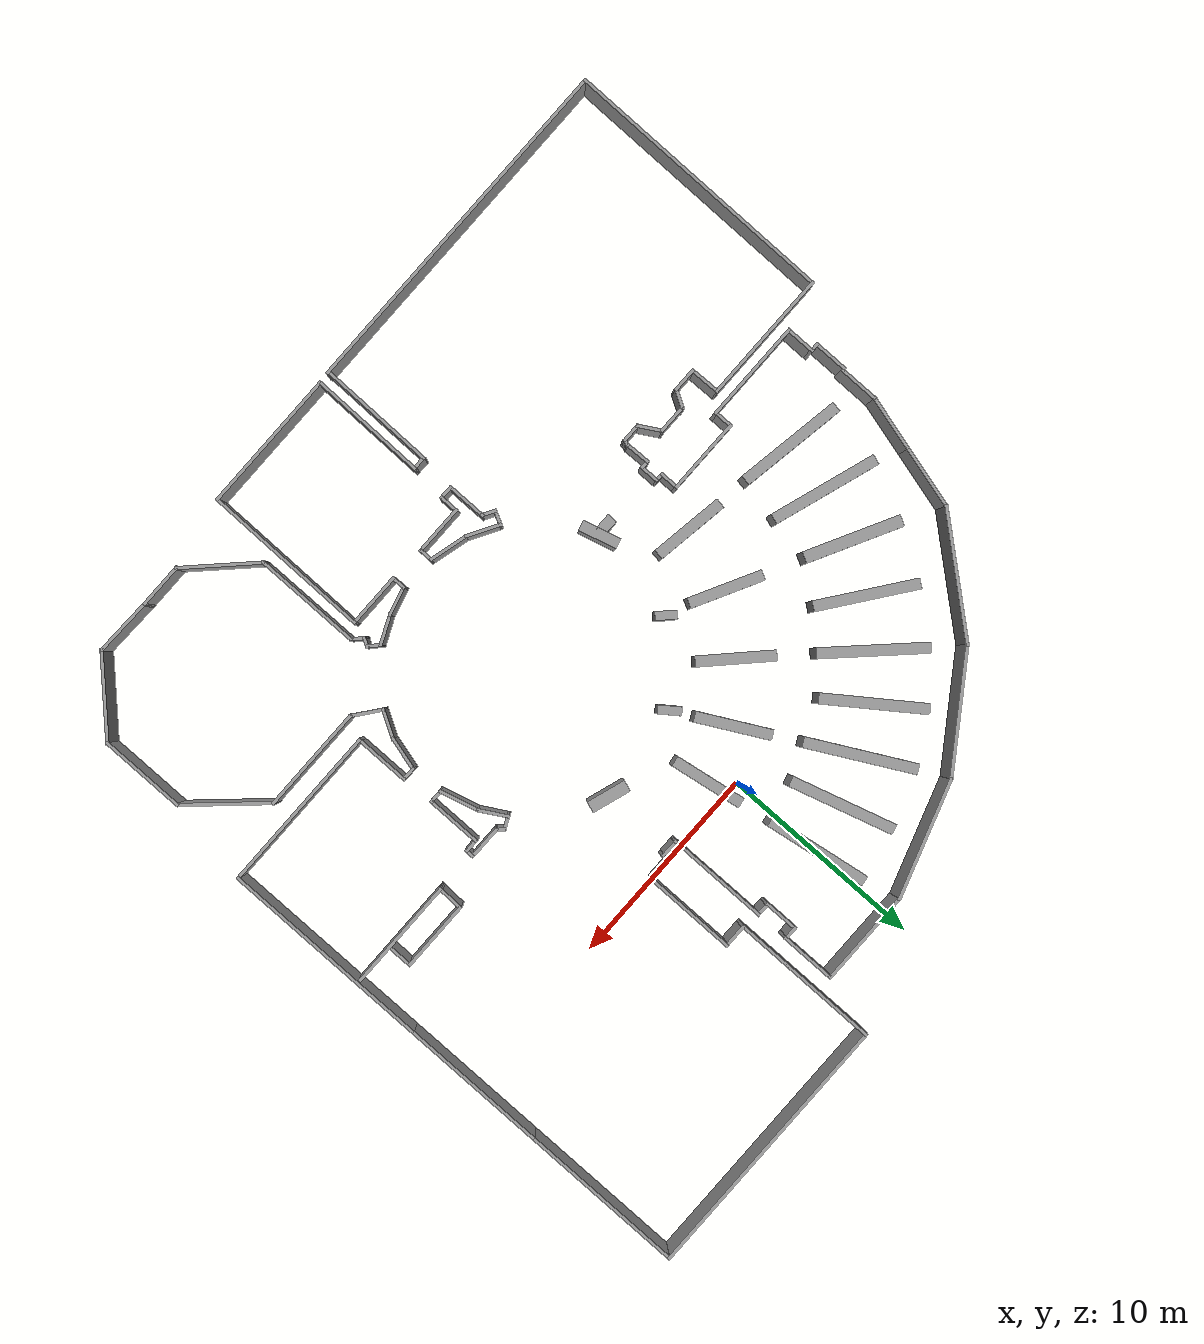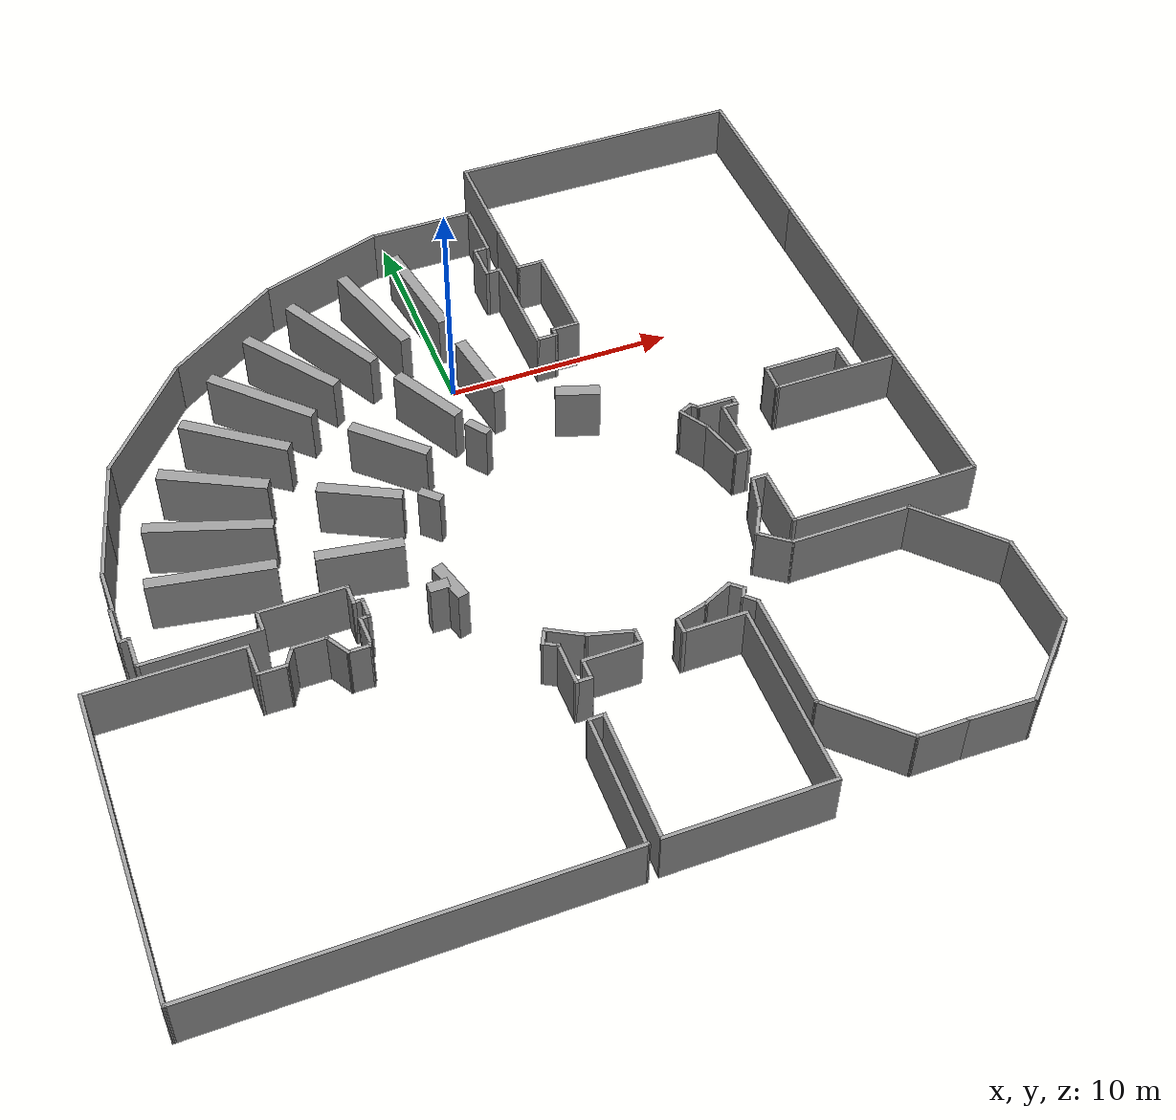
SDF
<?xml version='1.0'?>
<sdf version='1.7'>
  <model name='libraryModel'>
    <pose>-0.520895 -7.15339 0 0 -0 0</pose>
    <link name='Wall_1'>
      <collision name='Wall_1_Collision'>
        <geometry>
          <box>
            <size>6.5 0.15 2.5</size>
          </box>
        </geometry>
        <pose>0 0 1.25 0 -0 0</pose>
      </collision>
      <visual name='Wall_1_Visual'>
        <pose>0 0 1.25 0 -0 0</pose>
        <geometry>
          <box>
            <size>6.5 0.15 2.5</size>
          </box>
        </geometry>
        <material>
          <script>
            <uri>file://media/materials/scripts/gazebo.material</uri>
            <name>Gazebo/Grey</name>
          </script>
          <ambient>1 1 1 1</ambient>
        </material>
        <meta>
          <layer>0</layer>
        </meta>
      </visual>
      <pose>-14.9713 -5.1242 0 0 -0 0</pose>
    </link>
    <link name='Wall_10'>
      <collision name='Wall_10_Collision'>
        <geometry>
          <box>
            <size>1 0.15 2.5</size>
          </box>
        </geometry>
        <pose>0 0 1.25 0 -0 0</pose>
      </collision>
      <visual name='Wall_10_Visual'>
        <pose>0 0 1.25 0 -0 0</pose>
        <geometry>
          <box>
            <size>1 0.15 2.5</size>
          </box>
        </geometry>
        <material>
          <script>
            <uri>file://media/materials/scripts/gazebo.material</uri>
            <name>Gazebo/Grey</name>
          </script>
          <ambient>1 1 1 1</ambient>
        </material>
        <meta>
          <layer>0</layer>
        </meta>
      </visual>
      <pose>-7.44635 -4.0992 0 0 -0 1.5708</pose>
    </link>
    <link name='Wall_101'>
      <collision name='Wall_101_Collision'>
        <geometry>
          <box>
            <size>1.5 0.15 2.5</size>
          </box>
        </geometry>
        <pose>0 0 1.25 0 -0 0</pose>
      </collision>
      <visual name='Wall_101_Visual'>
        <pose>0 0 1.25 0 -0 0</pose>
        <geometry>
          <box>
            <size>1.5 0.15 2.5</size>
          </box>
        </geometry>
        <material>
          <script>
            <uri>file://media/materials/scripts/gazebo.material</uri>
            <name>Gazebo/Grey</name>
          </script>
          <ambient>1 1 1 1</ambient>
        </material>
        <meta>
          <layer>0</layer>
        </meta>
      </visual>
      <pose>8.65885 -0.242249 0 0 -0 -1.0472</pose>
    </link>
    <link name='Wall_102'>
      <collision name='Wall_102_Collision'>
        <geometry>
          <box>
            <size>2 0.15 2.5</size>
          </box>
        </geometry>
        <pose>0 0 1.25 0 -0 0</pose>
      </collision>
      <visual name='Wall_102_Visual'>
        <pose>0 0 1.25 0 -0 0</pose>
        <geometry>
          <box>
            <size>2 0.15 2.5</size>
          </box>
        </geometry>
        <material>
          <script>
            <uri>file://media/materials/scripts/gazebo.material</uri>
            <name>Gazebo/Grey</name>
          </script>
          <ambient>1 1 1 1</ambient>
        </material>
        <meta>
          <layer>0</layer>
        </meta>
      </visual>
      <pose>9.23576 -1.7203 0 0 -0 -1.309</pose>
    </link>
    <link name='Wall_103'>
      <collision name='Wall_103_Collision'>
        <geometry>
          <box>
            <size>0.75 0.15 2.5</size>
          </box>
        </geometry>
        <pose>0 0 1.25 0 -0 0</pose>
      </collision>
      <visual name='Wall_103_Visual'>
        <pose>0 0 1.25 0 -0 0</pose>
        <geometry>
          <box>
            <size>0.75 0.15 2.5</size>
          </box>
        </geometry>
        <material>
          <script>
            <uri>file://media/materials/scripts/gazebo.material</uri>
            <name>Gazebo/Grey</name>
          </script>
          <ambient>1 1 1 1</ambient>
        </material>
        <meta>
          <layer>0</layer>
        </meta>
      </visual>
      <pose>9.77517 -2.61378 0 0 -0 0</pose>
    </link>
    <link name='Wall_104'>
      <collision name='Wall_104_Collision'>
        <geometry>
          <box>
            <size>2.75 0.15 2.5</size>
          </box>
        </geometry>
        <pose>0 0 1.25 0 -0 0</pose>
      </collision>
      <visual name='Wall_104_Visual'>
        <pose>0 0 1.25 0 -0 0</pose>
        <geometry>
          <box>
            <size>2.75 0.15 2.5</size>
          </box>
        </geometry>
        <material>
          <script>
            <uri>file://media/materials/scripts/gazebo.material</uri>
            <name>Gazebo/Grey</name>
          </script>
          <ambient>1 1 1 1</ambient>
        </material>
        <meta>
          <layer>0</layer>
        </meta>
      </visual>
      <pose>10.0752 -1.31378 0 0 -0 1.5708</pose>
    </link>
    <link name='Wall_105'>
      <collision name='Wall_105_Collision'>
        <geometry>
          <box>
            <size>0.75 0.15 2.5</size>
          </box>
        </geometry>
        <pose>0 0 1.25 0 -0 0</pose>
      </collision>
      <visual name='Wall_105_Visual'>
        <pose>0 0 1.25 0 -0 0</pose>
        <geometry>
          <box>
            <size>0.75 0.15 2.5</size>
          </box>
        </geometry>
        <material>
          <script>
            <uri>file://media/materials/scripts/gazebo.material</uri>
            <name>Gazebo/Grey</name>
          </script>
          <ambient>1 1 1 1</ambient>
        </material>
        <meta>
          <layer>0</layer>
        </meta>
      </visual>
      <pose>10.3752 -0.013779 0 0 -0 0</pose>
    </link>
    <link name='Wall_106'>
      <collision name='Wall_106_Collision'>
        <geometry>
          <box>
            <size>0.5 0.15 2.5</size>
          </box>
        </geometry>
        <pose>0 0 1.25 0 -0 0</pose>
      </collision>
      <visual name='Wall_106_Visual'>
        <pose>0 0 1.25 0 -0 0</pose>
        <geometry>
          <box>
            <size>0.5 0.15 2.5</size>
          </box>
        </geometry>
        <material>
          <script>
            <uri>file://media/materials/scripts/gazebo.material</uri>
            <name>Gazebo/Grey</name>
          </script>
          <ambient>1 1 1 1</ambient>
        </material>
        <meta>
          <layer>0</layer>
        </meta>
      </visual>
      <pose>10.6752 0.161222 0 0 -0 1.5708</pose>
    </link>
    <link name='Wall_107'>
      <collision name='Wall_107_Collision'>
        <geometry>
          <box>
            <size>1.71407 0.15 2.5</size>
          </box>
        </geometry>
        <pose>0 0 1.25 0 -0 0</pose>
      </collision>
      <visual name='Wall_107_Visual'>
        <pose>0 0 1.25 0 -0 0</pose>
        <geometry>
          <box>
            <size>1.71407 0.15 2.5</size>
          </box>
        </geometry>
        <material>
          <script>
            <uri>file://media/materials/scripts/gazebo.material</uri>
            <name>Gazebo/Grey</name>
          </script>
          <ambient>1 1 1 1</ambient>
        </material>
        <meta>
          <layer>0</layer>
        </meta>
      </visual>
      <pose>9.89314 0.33927 0 0 -0 3.13769</pose>
    </link>
    <link name='Wall_108'>
      <collision name='Wall_108_Collision'>
        <geometry>
          <box>
            <size>0.5 0.15 2.5</size>
          </box>
        </geometry>
        <pose>0 0 1.25 0 -0 0</pose>
      </collision>
      <visual name='Wall_108_Visual'>
        <pose>0 0 1.25 0 -0 0</pose>
        <geometry>
          <box>
            <size>0.5 0.15 2.5</size>
          </box>
        </geometry>
        <material>
          <script>
            <uri>file://media/materials/scripts/gazebo.material</uri>
            <name>Gazebo/Grey</name>
          </script>
          <ambient>1 1 1 1</ambient>
        </material>
        <meta>
          <layer>0</layer>
        </meta>
      </visual>
      <pose>8.98736 0.466062 0 0 -0 2.35619</pose>
    </link>
    <link name='Wall_109'>
      <collision name='Wall_109_Collision'>
        <geometry>
          <box>
            <size>0.746074 0.15 2.5</size>
          </box>
        </geometry>
        <pose>0 0 1.25 0 -0 0</pose>
      </collision>
      <visual name='Wall_109_Visual'>
        <pose>0 0 1.25 0 -0 0</pose>
        <geometry>
          <box>
            <size>0.746074 0.15 2.5</size>
          </box>
        </geometry>
        <material>
          <script>
            <uri>file://media/materials/scripts/gazebo.material</uri>
            <name>Gazebo/Grey</name>
          </script>
          <ambient>1 1 1 1</ambient>
        </material>
        <meta>
          <layer>0</layer>
        </meta>
      </visual>
      <pose>8.59248 0.466062 0 0 -0 -2.71344</pose>
    </link>
    <link name='Wall_11'>
      <collision name='Wall_11_Collision'>
        <geometry>
          <box>
            <size>3.75 0.15 2.5</size>
          </box>
        </geometry>
        <pose>0 0 1.25 0 -0 0</pose>
      </collision>
      <visual name='Wall_11_Visual'>
        <pose>0 0 1.25 0 -0 0</pose>
        <geometry>
          <box>
            <size>3.75 0.15 2.5</size>
          </box>
        </geometry>
        <material>
          <script>
            <uri>file://media/materials/scripts/gazebo.material</uri>
            <name>Gazebo/Grey</name>
          </script>
          <ambient>1 1 1 1</ambient>
        </material>
        <meta>
          <layer>0</layer>
        </meta>
      </visual>
      <pose>-9.24635 -3.6742 0 0 -0 3.14159</pose>
    </link>
    <link name='Wall_111'>
      <collision name='Wall_111_Collision'>
        <geometry>
          <box>
            <size>5.5 0.15 2.5</size>
          </box>
        </geometry>
        <pose>0 0 1.25 0 -0 0</pose>
      </collision>
      <visual name='Wall_111_Visual'>
        <pose>0 0 1.25 0 -0 0</pose>
        <geometry>
          <box>
            <size>5.5 0.15 2.5</size>
          </box>
        </geometry>
        <material>
          <script>
            <uri>file://media/materials/scripts/gazebo.material</uri>
            <name>Gazebo/Grey</name>
          </script>
          <ambient>1 1 1 1</ambient>
        </material>
        <meta>
          <layer>0</layer>
        </meta>
      </visual>
      <pose>15.3789 0.231085 0 0 -0 0</pose>
    </link>
    <link name='Wall_115'>
      <collision name='Wall_115_Collision'>
        <geometry>
          <box>
            <size>1.8503 0.5 2.5</size>
          </box>
        </geometry>
        <pose>0 0 1.25 0 -0 0</pose>
      </collision>
      <visual name='Wall_115_Visual'>
        <pose>0 0 1.25 0 -0 0</pose>
        <geometry>
          <box>
            <size>1.8503 0.5 2.5</size>
          </box>
        </geometry>
        <material>
          <script>
            <uri>file://media/materials/scripts/gazebo.material</uri>
            <name>Gazebo/Grey</name>
          </script>
          <ambient>1 1 1 1</ambient>
        </material>
        <meta>
          <layer>0</layer>
        </meta>
      </visual>
      <pose>-3.6461 -4.83761 0 0 -0 1.83302</pose>
    </link>
    <link name='Wall_117'>
      <collision name='Wall_117_Collision'>
        <geometry>
          <box>
            <size>0.849678 0.5 2.5</size>
          </box>
        </geometry>
        <pose>0 0 1.25 0 -0 0</pose>
      </collision>
      <visual name='Wall_117_Visual'>
        <pose>0 0 1.25 0 -0 0</pose>
        <geometry>
          <box>
            <size>0.849678 0.5 2.5</size>
          </box>
        </geometry>
        <material>
          <script>
            <uri>file://media/materials/scripts/gazebo.material</uri>
            <name>Gazebo/Grey</name>
          </script>
          <ambient>1 1 1 1</ambient>
        </material>
        <meta>
          <layer>0</layer>
        </meta>
      </visual>
      <pose>-4.13511 -4.89061 0 0 -0 0</pose>
    </link>
    <link name='Wall_12'>
      <collision name='Wall_12_Collision'>
        <geometry>
          <box>
            <size>1 0.15 2.5</size>
          </box>
        </geometry>
        <pose>0 0 1.25 0 -0 0</pose>
      </collision>
      <visual name='Wall_12_Visual'>
        <pose>0 0 1.25 0 -0 0</pose>
        <geometry>
          <box>
            <size>1 0.15 2.5</size>
          </box>
        </geometry>
        <material>
          <script>
            <uri>file://media/materials/scripts/gazebo.material</uri>
            <name>Gazebo/Grey</name>
          </script>
          <ambient>1 1 1 1</ambient>
        </material>
        <meta>
          <layer>0</layer>
        </meta>
      </visual>
      <pose>-11.0463 -4.0992 0 0 -0 -1.5708</pose>
    </link>
    <link name='Wall_120'>
      <collision name='Wall_120_Collision'>
        <geometry>
          <box>
            <size>1.25 0.15 2.5</size>
          </box>
        </geometry>
        <pose>0 0 1.25 0 -0 0</pose>
      </collision>
      <visual name='Wall_120_Visual'>
        <pose>0 0 1.25 0 -0 0</pose>
        <geometry>
          <box>
            <size>1.25 0.15 2.5</size>
          </box>
        </geometry>
        <material>
          <script>
            <uri>file://media/materials/scripts/gazebo.material</uri>
            <name>Gazebo/Grey</name>
          </script>
          <ambient>1 1 1 1</ambient>
        </material>
        <meta>
          <layer>0</layer>
        </meta>
      </visual>
      <pose>-11.2176 -6.52441 0 0 -0 0</pose>
    </link>
    <link name='Wall_121'>
      <collision name='Wall_121_Collision'>
        <geometry>
          <box>
            <size>1 0.15 2.5</size>
          </box>
        </geometry>
        <pose>0 0 1.25 0 -0 0</pose>
      </collision>
      <visual name='Wall_121_Visual'>
        <pose>0 0 1.25 0 -0 0</pose>
        <geometry>
          <box>
            <size>1 0.15 2.5</size>
          </box>
        </geometry>
        <material>
          <script>
            <uri>file://media/materials/scripts/gazebo.material</uri>
            <name>Gazebo/Grey</name>
          </script>
          <ambient>1 1 1 1</ambient>
        </material>
        <meta>
          <layer>0</layer>
        </meta>
      </visual>
      <pose>-10.4551 -6.15635 0 0 -0 1.0472</pose>
    </link>
    <link name='Wall_122'>
      <collision name='Wall_122_Collision'>
        <geometry>
          <box>
            <size>1.5 0.15 2.5</size>
          </box>
        </geometry>
        <pose>0 0 1.25 0 -0 0</pose>
      </collision>
      <visual name='Wall_122_Visual'>
        <pose>0 0 1.25 0 -0 0</pose>
        <geometry>
          <box>
            <size>1.5 0.15 2.5</size>
          </box>
        </geometry>
        <material>
          <script>
            <uri>file://media/materials/scripts/gazebo.material</uri>
            <name>Gazebo/Grey</name>
          </script>
          <ambient>1 1 1 1</ambient>
        </material>
        <meta>
          <layer>0</layer>
        </meta>
      </visual>
      <pose>-9.56757 -5.78829 0 0 -0 0</pose>
    </link>
    <link name='Wall_123'>
      <collision name='Wall_123_Collision'>
        <geometry>
          <box>
            <size>1.25 0.15 2.5</size>
          </box>
        </geometry>
        <pose>0 0 1.25 0 -0 0</pose>
      </collision>
      <visual name='Wall_123_Visual'>
        <pose>0 0 1.25 0 -0 0</pose>
        <geometry>
          <box>
            <size>1.25 0.15 2.5</size>
          </box>
        </geometry>
        <material>
          <script>
            <uri>file://media/materials/scripts/gazebo.material</uri>
            <name>Gazebo/Grey</name>
          </script>
          <ambient>1 1 1 1</ambient>
        </material>
        <meta>
          <layer>0</layer>
        </meta>
      </visual>
      <pose>-8.61757 -6.26461 0 0 -0 -1.0472</pose>
    </link>
    <link name='Wall_124'>
      <collision name='Wall_124_Collision'>
        <geometry>
          <box>
            <size>1 0.15 2.5</size>
          </box>
        </geometry>
        <pose>0 0 1.25 0 -0 0</pose>
      </collision>
      <visual name='Wall_124_Visual'>
        <pose>0 0 1.25 0 -0 0</pose>
        <geometry>
          <box>
            <size>1 0.15 2.5</size>
          </box>
        </geometry>
        <material>
          <script>
            <uri>file://media/materials/scripts/gazebo.material</uri>
            <name>Gazebo/Grey</name>
          </script>
          <ambient>1 1 1 1</ambient>
        </material>
        <meta>
          <layer>0</layer>
        </meta>
      </visual>
      <pose>-7.91757 -6.74092 0 0 -0 0</pose>
    </link>
    <link name='Wall_125'>
      <collision name='Wall_125_Collision'>
        <geometry>
          <box>
            <size>0.379129 0.15 2.5</size>
          </box>
        </geometry>
        <pose>0 0 1.25 0 -0 0</pose>
      </collision>
      <visual name='Wall_125_Visual'>
        <pose>0 0 1.25 0 -0 0</pose>
        <geometry>
          <box>
            <size>0.379129 0.15 2.5</size>
          </box>
        </geometry>
        <material>
          <script>
            <uri>file://media/materials/scripts/gazebo.material</uri>
            <name>Gazebo/Grey</name>
          </script>
          <ambient>1 1 1 1</ambient>
        </material>
        <meta>
          <layer>0</layer>
        </meta>
      </visual>
      <pose>-7.45507 -6.63267 0 0 -0 1.23732</pose>
    </link>
    <link name='Wall_127'>
      <collision name='Wall_127_Collision'>
        <geometry>
          <box>
            <size>5.22507 0.5 2.5</size>
          </box>
        </geometry>
        <pose>0 0 1.25 0 -0 0</pose>
      </collision>
      <visual name='Wall_127_Visual'>
        <pose>0 0 1.25 0 -0 0</pose>
        <geometry>
          <box>
            <size>5.22507 0.5 2.5</size>
          </box>
        </geometry>
        <material>
          <script>
            <uri>file://media/materials/scripts/gazebo.material</uri>
            <name>Gazebo/Grey</name>
          </script>
          <ambient>1 1 1 1</ambient>
        </material>
        <meta>
          <layer>0</layer>
        </meta>
      </visual>
      <pose>-3.93287 10.2258 0 0 -0 -1.08254</pose>
    </link>
    <link name='Wall_129'>
      <collision name='Wall_129_Collision'>
        <geometry>
          <box>
            <size>4.93346 0.5 2.5</size>
          </box>
        </geometry>
        <pose>0 0 1.25 0 -0 0</pose>
      </collision>
      <visual name='Wall_129_Visual'>
        <pose>0 0 1.25 0 -0 0</pose>
        <geometry>
          <box>
            <size>4.93346 0.5 2.5</size>
          </box>
        </geometry>
        <material>
          <script>
            <uri>file://media/materials/scripts/gazebo.material</uri>
            <name>Gazebo/Grey</name>
          </script>
          <ambient>1 1 1 1</ambient>
        </material>
        <meta>
          <layer>0</layer>
        </meta>
      </visual>
      <pose>-6.04805 9.1613 0 0 -0 -0.94688</pose>
    </link>
    <link name='Wall_13'>
      <collision name='Wall_13_Collision'>
        <geometry>
          <box>
            <size>5 0.15 2.5</size>
          </box>
        </geometry>
        <pose>0 0 1.25 0 -0 0</pose>
      </collision>
      <visual name='Wall_13_Visual'>
        <pose>0 0 1.25 0 -0 0</pose>
        <geometry>
          <box>
            <size>5 0.15 2.5</size>
          </box>
        </geometry>
        <material>
          <script>
            <uri>file://media/materials/scripts/gazebo.material</uri>
            <name>Gazebo/Grey</name>
          </script>
          <ambient>1 1 1 1</ambient>
        </material>
        <meta>
          <layer>0</layer>
        </meta>
      </visual>
      <pose>-13.4713 -4.5242 0 0 -0 3.14159</pose>
    </link>
    <link name='Wall_131'>
      <collision name='Wall_131_Collision'>
        <geometry>
          <box>
            <size>5.07999 0.5 2.5</size>
          </box>
        </geometry>
        <pose>0 0 1.25 0 -0 0</pose>
      </collision>
      <visual name='Wall_131_Visual'>
        <pose>0 0 1.25 0 -0 0</pose>
        <geometry>
          <box>
            <size>5.07999 0.5 2.5</size>
          </box>
        </geometry>
        <material>
          <script>
            <uri>file://media/materials/scripts/gazebo.material</uri>
            <name>Gazebo/Grey</name>
          </script>
          <ambient>1 1 1 1</ambient>
        </material>
        <meta>
          <layer>0</layer>
        </meta>
      </visual>
      <pose>-7.78959 7.59265 0 0 -0 -0.798745</pose>
    </link>
    <link name='Wall_133'>
      <collision name='Wall_133_Collision'>
        <geometry>
          <box>
            <size>4.8492 0.5 2.5</size>
          </box>
        </geometry>
        <pose>0 0 1.25 0 -0 0</pose>
      </collision>
      <visual name='Wall_133_Visual'>
        <pose>0 0 1.25 0 -0 0</pose>
        <geometry>
          <box>
            <size>4.8492 0.5 2.5</size>
          </box>
        </geometry>
        <material>
          <script>
            <uri>file://media/materials/scripts/gazebo.material</uri>
            <name>Gazebo/Grey</name>
          </script>
          <ambient>1 1 1 1</ambient>
        </material>
        <meta>
          <layer>0</layer>
        </meta>
      </visual>
      <pose>-9.4245 5.75038 0 0 -0 -0.638036</pose>
    </link>
    <link name='Wall_135'>
      <collision name='Wall_135_Collision'>
        <geometry>
          <box>
            <size>4.61323 0.55 2.5</size>
          </box>
        </geometry>
        <pose>0 0 1.25 0 -0 0</pose>
      </collision>
      <visual name='Wall_135_Visual'>
        <pose>0 0 1.25 0 -0 0</pose>
        <geometry>
          <box>
            <size>4.61323 0.55 2.5</size>
          </box>
        </geometry>
        <material>
          <script>
            <uri>file://media/materials/scripts/gazebo.material</uri>
            <name>Gazebo/Grey</name>
          </script>
          <ambient>1 1 1 1</ambient>
        </material>
        <meta>
          <layer>0</layer>
        </meta>
      </visual>
      <pose>-10.8759 3.67924 0 0 -0 2.65712</pose>
    </link>
    <link name='Wall_137'>
      <collision name='Wall_137_Collision'>
        <geometry>
          <box>
            <size>5.21597 0.5 2.5</size>
          </box>
        </geometry>
        <pose>0 0 1.25 0 -0 0</pose>
      </collision>
      <visual name='Wall_137_Visual'>
        <pose>0 0 1.25 0 -0 0</pose>
        <geometry>
          <box>
            <size>5.21597 0.5 2.5</size>
          </box>
        </geometry>
        <material>
          <script>
            <uri>file://media/materials/scripts/gazebo.material</uri>
            <name>Gazebo/Grey</name>
          </script>
          <ambient>1 1 1 1</ambient>
        </material>
        <meta>
          <layer>0</layer>
        </meta>
      </visual>
      <pose>-11.6954 1.29706 0 0 -0 -0.319369</pose>
    </link>
    <link name='Wall_139'>
      <collision name='Wall_139_Collision'>
        <geometry>
          <box>
            <size>5.16361 0.5 2.5</size>
          </box>
        </geometry>
        <pose>0 0 1.25 0 -0 0</pose>
      </collision>
      <visual name='Wall_139_Visual'>
        <pose>0 0 1.25 0 -0 0</pose>
        <geometry>
          <box>
            <size>5.16361 0.5 2.5</size>
          </box>
        </geometry>
        <material>
          <script>
            <uri>file://media/materials/scripts/gazebo.material</uri>
            <name>Gazebo/Grey</name>
          </script>
          <ambient>1 1 1 1</ambient>
        </material>
        <meta>
          <layer>0</layer>
        </meta>
      </visual>
      <pose>-12.2101 -1.15593 0 0 -0 -0.16715</pose>
    </link>
    <link name='Wall_14'>
      <collision name='Wall_14_Collision'>
        <geometry>
          <box>
            <size>1.5 0.15 2.5</size>
          </box>
        </geometry>
        <pose>0 0 1.25 0 -0 0</pose>
      </collision>
      <visual name='Wall_14_Visual'>
        <pose>0 0 1.25 0 -0 0</pose>
        <geometry>
          <box>
            <size>1.5 0.15 2.5</size>
          </box>
        </geometry>
        <material>
          <script>
            <uri>file://media/materials/scripts/gazebo.material</uri>
            <name>Gazebo/Grey</name>
          </script>
          <ambient>1 1 1 1</ambient>
        </material>
        <meta>
          <layer>0</layer>
        </meta>
      </visual>
      <pose>-15.8963 -3.8492 0 0 -0 1.5708</pose>
    </link>
    <link name='Wall_141'>
      <collision name='Wall_141_Collision'>
        <geometry>
          <box>
            <size>3.55121 0.5 2.5</size>
          </box>
        </geometry>
        <pose>0 0 1.25 0 -0 0</pose>
      </collision>
      <visual name='Wall_141_Visual'>
        <pose>0 0 1.25 0 -0 0</pose>
        <geometry>
          <box>
            <size>3.55121 0.5 2.5</size>
          </box>
        </geometry>
        <material>
          <script>
            <uri>file://media/materials/scripts/gazebo.material</uri>
            <name>Gazebo/Grey</name>
          </script>
          <ambient>1 1 1 1</ambient>
        </material>
        <meta>
          <layer>0</layer>
        </meta>
      </visual>
      <pose>-6.4409 -2.02681 0 0 -0 -0.155446</pose>
    </link>
    <link name='Wall_143'>
      <collision name='Wall_143_Collision'>
        <geometry>
          <box>
            <size>3.51982 0.5 2.5</size>
          </box>
        </geometry>
        <pose>0 0 1.25 0 -0 0</pose>
      </collision>
      <visual name='Wall_143_Visual'>
        <pose>0 0 1.25 0 -0 0</pose>
        <geometry>
          <box>
            <size>3.51982 0.5 2.5</size>
          </box>
        </geometry>
        <material>
          <script>
            <uri>file://media/materials/scripts/gazebo.material</uri>
            <name>Gazebo/Grey</name>
          </script>
          <ambient>1 1 1 1</ambient>
        </material>
        <meta>
          <layer>0</layer>
        </meta>
      </visual>
      <pose>-5.51879 0.933116 0 0 -0 -0.483926</pose>
    </link>
    <link name='Wall_145'>
      <collision name='Wall_145_Collision'>
        <geometry>
          <box>
            <size>3.61835 0.5 2.5</size>
          </box>
        </geometry>
        <pose>0 0 1.25 0 -0 0</pose>
      </collision>
      <visual name='Wall_145_Visual'>
        <pose>0 0 1.25 0 -0 0</pose>
        <geometry>
          <box>
            <size>3.61835 0.5 2.5</size>
          </box>
        </geometry>
        <material>
          <script>
            <uri>file://media/materials/scripts/gazebo.material</uri>
            <name>Gazebo/Grey</name>
          </script>
          <ambient>1 1 1 1</ambient>
        </material>
        <meta>
          <layer>0</layer>
        </meta>
      </visual>
      <pose>-3.51427 3.27261 0 0 -0 -0.772674</pose>
    </link>
    <link name='Wall_147'>
      <collision name='Wall_147_Collision'>
        <geometry>
          <box>
            <size>3.54199 0.5 2.5</size>
          </box>
        </geometry>
        <pose>0 0 1.25 0 -0 0</pose>
      </collision>
      <visual name='Wall_147_Visual'>
        <pose>0 0 1.25 0 -0 0</pose>
        <geometry>
          <box>
            <size>3.54199 0.5 2.5</size>
          </box>
        </geometry>
        <material>
          <script>
            <uri>file://media/materials/scripts/gazebo.material</uri>
            <name>Gazebo/Grey</name>
          </script>
          <ambient>1 1 1 1</ambient>
        </material>
        <meta>
          <layer>0</layer>
        </meta>
      </visual>
      <pose>-1.21875 5.15505 0 0 -0 -1.08263</pose>
    </link>
    <link name='Wall_149'>
      <collision name='Wall_149_Collision'>
        <geometry>
          <box>
            <size>3.46346 0.5 2.5</size>
          </box>
        </geometry>
        <pose>0 0 1.25 0 -0 0</pose>
      </collision>
      <visual name='Wall_149_Visual'>
        <pose>0 0 1.25 0 -0 0</pose>
        <geometry>
          <box>
            <size>3.46346 0.5 2.5</size>
          </box>
        </geometry>
        <material>
          <script>
            <uri>file://media/materials/scripts/gazebo.material</uri>
            <name>Gazebo/Grey</name>
          </script>
          <ambient>1 1 1 1</ambient>
        </material>
        <meta>
          <layer>0</layer>
        </meta>
      </visual>
      <pose>1.38052 5.95619 0 0 -0 -1.41247</pose>
    </link>
    <link name='Wall_15'>
      <collision name='Wall_15_Collision'>
        <geometry>
          <box>
            <size>0.5 0.15 2.5</size>
          </box>
        </geometry>
        <pose>0 0 1.25 0 -0 0</pose>
      </collision>
      <visual name='Wall_15_Visual'>
        <pose>0 0 1.25 0 -0 0</pose>
        <geometry>
          <box>
            <size>0.5 0.15 2.5</size>
          </box>
        </geometry>
        <material>
          <script>
            <uri>file://media/materials/scripts/gazebo.material</uri>
            <name>Gazebo/Grey</name>
          </script>
          <ambient>1 1 1 1</ambient>
        </material>
        <meta>
          <layer>0</layer>
        </meta>
      </visual>
      <pose>-16.0713 -3.1742 0 0 -0 3.14159</pose>
    </link>
    <link name='Wall_152'>
      <collision name='Wall_152_Collision'>
        <geometry>
          <box>
            <size>5.03352 0.5 2.5</size>
          </box>
        </geometry>
        <pose>0 0 1.25 0 -0 0</pose>
      </collision>
      <visual name='Wall_152_Visual'>
        <pose>0 0 1.25 0 -0 0</pose>
        <geometry>
          <box>
            <size>5.03352 0.5 2.5</size>
          </box>
        </geometry>
        <material>
          <script>
            <uri>file://media/materials/scripts/gazebo.material</uri>
            <name>Gazebo/Grey</name>
          </script>
          <ambient>1 1 1 1</ambient>
        </material>
        <meta>
          <layer>0</layer>
        </meta>
      </visual>
      <pose>-1.76386 11.0787 0 0 -0 -1.28734</pose>
    </link>
    <link name='Wall_154'>
      <collision name='Wall_154_Collision'>
        <geometry>
          <box>
            <size>4.92429 0.5 2.5</size>
          </box>
        </geometry>
        <pose>0 0 1.25 0 -0 0</pose>
      </collision>
      <visual name='Wall_154_Visual'>
        <pose>0 0 1.25 0 -0 0</pose>
        <geometry>
          <box>
            <size>4.92429 0.5 2.5</size>
          </box>
        </geometry>
        <material>
          <script>
            <uri>file://media/materials/scripts/gazebo.material</uri>
            <name>Gazebo/Grey</name>
          </script>
          <ambient>1 1 1 1</ambient>
        </material>
        <meta>
          <layer>0</layer>
        </meta>
      </visual>
      <pose>0.478676 11.5802 0 0 -0 -1.4162</pose>
    </link>
    <link name='Wall_157'>
      <collision name='Wall_157_Collision'>
        <geometry>
          <box>
            <size>1.25 0.15 2.5</size>
          </box>
        </geometry>
        <pose>0 0 1.25 0 -0 0</pose>
      </collision>
      <visual name='Wall_157_Visual'>
        <pose>0 0 1.25 0 -0 0</pose>
        <geometry>
          <box>
            <size>1.25 0.15 2.5</size>
          </box>
        </geometry>
        <material>
          <script>
            <uri>file://media/materials/scripts/gazebo.material</uri>
            <name>Gazebo/Grey</name>
          </script>
          <ambient>1 1 1 1</ambient>
        </material>
        <meta>
          <layer>0</layer>
        </meta>
      </visual>
      <pose>16.0983 0.865296 0 0 -0 1.5708</pose>
    </link>
    <link name='Wall_158'>
      <collision name='Wall_158_Collision'>
        <geometry>
          <box>
            <size>3.5 0.15 2.5</size>
          </box>
        </geometry>
        <pose>0 0 1.25 0 -0 0</pose>
      </collision>
      <visual name='Wall_158_Visual'>
        <pose>0 0 1.25 0 -0 0</pose>
        <geometry>
          <box>
            <size>3.5 0.15 2.5</size>
          </box>
        </geometry>
        <material>
          <script>
            <uri>file://media/materials/scripts/gazebo.material</uri>
            <name>Gazebo/Grey</name>
          </script>
          <ambient>1 1 1 1</ambient>
        </material>
        <meta>
          <layer>0</layer>
        </meta>
      </visual>
      <pose>14.4233 1.4153 0 0 -0 3.14159</pose>
    </link>
    <link name='Wall_159'>
      <collision name='Wall_159_Collision'>
        <geometry>
          <box>
            <size>1.33504 0.15 2.5</size>
          </box>
        </geometry>
        <pose>0 0 1.25 0 -0 0</pose>
      </collision>
      <visual name='Wall_159_Visual'>
        <pose>0 0 1.25 0 -0 0</pose>
        <geometry>
          <box>
            <size>1.33504 0.15 2.5</size>
          </box>
        </geometry>
        <material>
          <script>
            <uri>file://media/materials/scripts/gazebo.material</uri>
            <name>Gazebo/Grey</name>
          </script>
          <ambient>1 1 1 1</ambient>
        </material>
        <meta>
          <layer>0</layer>
        </meta>
      </visual>
      <pose>12.7261 0.823191 0 0 -0 -1.60824</pose>
    </link>
    <link name='Wall_16'>
      <collision name='Wall_16_Collision'>
        <geometry>
          <box>
            <size>1.75 0.15 2.5</size>
          </box>
        </geometry>
        <pose>0 0 1.25 0 -0 0</pose>
      </collision>
      <visual name='Wall_16_Visual'>
        <pose>0 0 1.25 0 -0 0</pose>
        <geometry>
          <box>
            <size>1.75 0.15 2.5</size>
          </box>
        </geometry>
        <material>
          <script>
            <uri>file://media/materials/scripts/gazebo.material</uri>
            <name>Gazebo/Grey</name>
          </script>
          <ambient>1 1 1 1</ambient>
        </material>
        <meta>
          <layer>0</layer>
        </meta>
      </visual>
      <pose>-16.2463 -2.3742 0 0 -0 1.5708</pose>
    </link>
    <link name='Wall_17'>
      <collision name='Wall_17_Collision'>
        <geometry>
          <box>
            <size>0.25 0.15 2.5</size>
          </box>
        </geometry>
        <pose>0 0 1.25 0 -0 0</pose>
      </collision>
      <visual name='Wall_17_Visual'>
        <pose>0 0 1.25 0 -0 0</pose>
        <geometry>
          <box>
            <size>0.25 0.15 2.5</size>
          </box>
        </geometry>
        <material>
          <script>
            <uri>file://media/materials/scripts/gazebo.material</uri>
            <name>Gazebo/Grey</name>
          </script>
          <ambient>1 1 1 1</ambient>
        </material>
        <meta>
          <layer>0</layer>
        </meta>
      </visual>
      <pose>-16.1963 -1.5742 0 0 -0 0</pose>
    </link>
    <link name='Wall_18'>
      <collision name='Wall_18_Collision'>
        <geometry>
          <box>
            <size>2 0.15 2.5</size>
          </box>
        </geometry>
        <pose>0 0 1.25 0 -0 0</pose>
      </collision>
      <visual name='Wall_18_Visual'>
        <pose>0 0 1.25 0 -0 0</pose>
        <geometry>
          <box>
            <size>2 0.15 2.5</size>
          </box>
        </geometry>
        <material>
          <script>
            <uri>file://media/materials/scripts/gazebo.material</uri>
            <name>Gazebo/Grey</name>
          </script>
          <ambient>1 1 1 1</ambient>
        </material>
        <meta>
          <layer>0</layer>
        </meta>
      </visual>
      <pose>-16.1463 -0.649204 0 0 -0 1.5708</pose>
    </link>
    <link name='Wall_19'>
      <collision name='Wall_19_Collision'>
        <geometry>
          <box>
            <size>2.75 0.15 2.5</size>
          </box>
        </geometry>
        <pose>0 0 1.25 0 -0 0</pose>
      </collision>
      <visual name='Wall_19_Visual'>
        <pose>0 0 1.25 0 -0 0</pose>
        <geometry>
          <box>
            <size>2.75 0.15 2.5</size>
          </box>
        </geometry>
        <material>
          <script>
            <uri>file://media/materials/scripts/gazebo.material</uri>
            <name>Gazebo/Grey</name>
          </script>
          <ambient>1 1 1 1</ambient>
        </material>
        <meta>
          <layer>0</layer>
        </meta>
      </visual>
      <pose>-15.8099 1.5315 0 0 -0 1.309</pose>
    </link>
    <link name='Wall_21'>
      <collision name='Wall_21_Collision'>
        <geometry>
          <box>
            <size>3.25 0.15 2.5</size>
          </box>
        </geometry>
        <pose>0 0 1.25 0 -0 0</pose>
      </collision>
      <visual name='Wall_21_Visual'>
        <pose>0 0 1.25 0 -0 0</pose>
        <geometry>
          <box>
            <size>3.25 0.15 2.5</size>
          </box>
        </geometry>
        <material>
          <script>
            <uri>file://media/materials/scripts/gazebo.material</uri>
            <name>Gazebo/Grey</name>
          </script>
          <ambient>1 1 1 1</ambient>
        </material>
        <meta>
          <layer>0</layer>
        </meta>
      </visual>
      <pose>-15.0723 4.28439 0 0 -0 1.309</pose>
    </link>
    <link name='Wall_22'>
      <collision name='Wall_22_Collision'>
        <geometry>
          <box>
            <size>6.32238 0.15 2.5</size>
          </box>
        </geometry>
        <pose>0 0 1.25 0 -0 0</pose>
      </collision>
      <visual name='Wall_22_Visual'>
        <pose>0 0 1.25 0 -0 0</pose>
        <geometry>
          <box>
            <size>6.32238 0.15 2.5</size>
          </box>
        </geometry>
        <material>
          <script>
            <uri>file://media/materials/scripts/gazebo.material</uri>
            <name>Gazebo/Grey</name>
          </script>
          <ambient>1 1 1 1</ambient>
        </material>
        <meta>
          <layer>0</layer>
        </meta>
      </visual>
      <pose>-12.6884 8.14661 0 0 -0 0.873106</pose>
    </link>
    <link name='Wall_24'>
      <collision name='Wall_24_Collision'>
        <geometry>
          <box>
            <size>6.12348 0.15 2.5</size>
          </box>
        </geometry>
        <pose>0 0 1.25 0 -0 0</pose>
      </collision>
      <visual name='Wall_24_Visual'>
        <pose>0 0 1.25 0 -0 0</pose>
        <geometry>
          <box>
            <size>6.12348 0.15 2.5</size>
          </box>
        </geometry>
        <material>
          <script>
            <uri>file://media/materials/scripts/gazebo.material</uri>
            <name>Gazebo/Grey</name>
          </script>
          <ambient>1 1 1 1</ambient>
        </material>
        <meta>
          <layer>0</layer>
        </meta>
      </visual>
      <pose>-8.24419 12.2034 0 0 -0 0.602142</pose>
    </link>
    <link name='Wall_25'>
      <collision name='Wall_25_Collision'>
        <geometry>
          <box>
            <size>5.89571 0.15 2.5</size>
          </box>
        </geometry>
        <pose>0 0 1.25 0 -0 0</pose>
      </collision>
      <visual name='Wall_25_Visual'>
        <pose>0 0 1.25 0 -0 0</pose>
        <geometry>
          <box>
            <size>5.89571 0.15 2.5</size>
          </box>
        </geometry>
        <material>
          <script>
            <uri>file://media/materials/scripts/gazebo.material</uri>
            <name>Gazebo/Grey</name>
          </script>
          <ambient>1 1 1 1</ambient>
        </material>
        <meta>
          <layer>0</layer>
        </meta>
      </visual>
      <pose>-3.05062 14.7832 0 0 -0 0.314302</pose>
    </link>
    <link name='Wall_26'>
      <collision name='Wall_26_Collision'>
        <geometry>
          <box>
            <size>4.75 0.15 2.5</size>
          </box>
        </geometry>
        <pose>0 0 1.25 0 -0 0</pose>
      </collision>
      <visual name='Wall_26_Visual'>
        <pose>0 0 1.25 0 -0 0</pose>
        <geometry>
          <box>
            <size>4.75 0.15 2.5</size>
          </box>
        </geometry>
        <material>
          <script>
            <uri>file://media/materials/scripts/gazebo.material</uri>
            <name>Gazebo/Grey</name>
          </script>
          <ambient>1 1 1 1</ambient>
        </material>
        <meta>
          <layer>0</layer>
        </meta>
      </visual>
      <pose>1.9817 15.6714 0 0 -0 2e-06</pose>
    </link>
    <link name='Wall_27'>
      <collision name='Wall_27_Collision'>
        <geometry>
          <box>
            <size>2.75 0.15 2.5</size>
          </box>
        </geometry>
        <pose>0 0 1.25 0 -0 0</pose>
      </collision>
      <visual name='Wall_27_Visual'>
        <pose>0 0 1.25 0 -0 0</pose>
        <geometry>
          <box>
            <size>2.75 0.15 2.5</size>
          </box>
        </geometry>
        <material>
          <script>
            <uri>file://media/materials/scripts/gazebo.material</uri>
            <name>Gazebo/Grey</name>
          </script>
          <ambient>1 1 1 1</ambient>
        </material>
        <meta>
          <layer>0</layer>
        </meta>
      </visual>
      <pose>4.28189 14.3714 0 0 -0 -1.5708</pose>
    </link>
    <link name='Wall_28'>
      <collision name='Wall_28_Collision'>
        <geometry>
          <box>
            <size>0.75 0.15 2.5</size>
          </box>
        </geometry>
        <pose>0 0 1.25 0 -0 0</pose>
      </collision>
      <visual name='Wall_28_Visual'>
        <pose>0 0 1.25 0 -0 0</pose>
        <geometry>
          <box>
            <size>0.75 0.15 2.5</size>
          </box>
        </geometry>
        <material>
          <script>
            <uri>file://media/materials/scripts/gazebo.material</uri>
            <name>Gazebo/Grey</name>
          </script>
          <ambient>1 1 1 1</ambient>
        </material>
        <meta>
          <layer>0</layer>
        </meta>
      </visual>
      <pose>3.9817 13.0714 0 0 -0 -3.14158</pose>
    </link>
    <link name='Wall_29'>
      <collision name='Wall_29_Collision'>
        <geometry>
          <box>
            <size>1.75 0.15 2.5</size>
          </box>
        </geometry>
        <pose>0 0 1.25 0 -0 0</pose>
      </collision>
      <visual name='Wall_29_Visual'>
        <pose>0 0 1.25 0 -0 0</pose>
        <geometry>
          <box>
            <size>1.75 0.15 2.5</size>
          </box>
        </geometry>
        <material>
          <script>
            <uri>file://media/materials/scripts/gazebo.material</uri>
            <name>Gazebo/Grey</name>
          </script>
          <ambient>1 1 1 1</ambient>
        </material>
        <meta>
          <layer>0</layer>
        </meta>
      </visual>
      <pose>3.6815 12.2714 0 0 -0 -1.5708</pose>
    </link>
    <link name='Wall_30'>
      <collision name='Wall_30_Collision'>
        <geometry>
          <box>
            <size>0.75 0.15 2.5</size>
          </box>
        </geometry>
        <pose>0 0 1.25 0 -0 0</pose>
      </collision>
      <visual name='Wall_30_Visual'>
        <pose>0 0 1.25 0 -0 0</pose>
        <geometry>
          <box>
            <size>0.75 0.15 2.5</size>
          </box>
        </geometry>
        <material>
          <script>
            <uri>file://media/materials/scripts/gazebo.material</uri>
            <name>Gazebo/Grey</name>
          </script>
          <ambient>1 1 1 1</ambient>
        </material>
        <meta>
          <layer>0</layer>
        </meta>
      </visual>
      <pose>3.9815 11.4714 0 0 -0 0</pose>
    </link>
    <link name='Wall_31'>
      <collision name='Wall_31_Collision'>
        <geometry>
          <box>
            <size>5 0.15 2.5</size>
          </box>
        </geometry>
        <pose>0 0 1.25 0 -0 0</pose>
      </collision>
      <visual name='Wall_31_Visual'>
        <pose>0 0 1.25 0 -0 0</pose>
        <geometry>
          <box>
            <size>5 0.15 2.5</size>
          </box>
        </geometry>
        <material>
          <script>
            <uri>file://media/materials/scripts/gazebo.material</uri>
            <name>Gazebo/Grey</name>
          </script>
          <ambient>1 1 1 1</ambient>
        </material>
        <meta>
          <layer>0</layer>
        </meta>
      </visual>
      <pose>4.2815 9.04638 0 0 -0 -1.5708</pose>
    </link>
    <link name='Wall_33'>
      <collision name='Wall_33_Collision'>
        <geometry>
          <box>
            <size>1 0.15 2.5</size>
          </box>
        </geometry>
        <pose>0 0 1.25 0 -0 0</pose>
      </collision>
      <visual name='Wall_33_Visual'>
        <pose>0 0 1.25 0 -0 0</pose>
        <geometry>
          <box>
            <size>1 0.15 2.5</size>
          </box>
        </geometry>
        <material>
          <script>
            <uri>file://media/materials/scripts/gazebo.material</uri>
            <name>Gazebo/Grey</name>
          </script>
          <ambient>1 1 1 1</ambient>
        </material>
        <meta>
          <layer>0</layer>
        </meta>
      </visual>
      <pose>4.7065 6.62138 0 0 -0 0</pose>
    </link>
    <link name='Wall_34'>
      <collision name='Wall_34_Collision'>
        <geometry>
          <box>
            <size>0.5 0.15 2.5</size>
          </box>
        </geometry>
        <pose>0 0 1.25 0 -0 0</pose>
      </collision>
      <visual name='Wall_34_Visual'>
        <pose>0 0 1.25 0 -0 0</pose>
        <geometry>
          <box>
            <size>0.5 0.15 2.5</size>
          </box>
        </geometry>
        <material>
          <script>
            <uri>file://media/materials/scripts/gazebo.material</uri>
            <name>Gazebo/Grey</name>
          </script>
          <ambient>1 1 1 1</ambient>
        </material>
        <meta>
          <layer>0</layer>
        </meta>
      </visual>
      <pose>5.1315 6.79638 0 0 -0 1.5708</pose>
    </link>
    <link name='Wall_35'>
      <collision name='Wall_35_Collision'>
        <geometry>
          <box>
            <size>1.25 0.15 2.5</size>
          </box>
        </geometry>
        <pose>0 0 1.25 0 -0 0</pose>
      </collision>
      <visual name='Wall_35_Visual'>
        <pose>0 0 1.25 0 -0 0</pose>
        <geometry>
          <box>
            <size>1.25 0.15 2.5</size>
          </box>
        </geometry>
        <material>
          <script>
            <uri>file://media/materials/scripts/gazebo.material</uri>
            <name>Gazebo/Grey</name>
          </script>
          <ambient>1 1 1 1</ambient>
        </material>
        <meta>
          <layer>0</layer>
        </meta>
      </visual>
      <pose>5.6815 6.97138 0 0 -0 0</pose>
    </link>
    <link name='Wall_36'>
      <collision name='Wall_36_Collision'>
        <geometry>
          <box>
            <size>4.5 0.15 2.5</size>
          </box>
        </geometry>
        <pose>0 0 1.25 0 -0 0</pose>
      </collision>
      <visual name='Wall_36_Visual'>
        <pose>0 0 1.25 0 -0 0</pose>
        <geometry>
          <box>
            <size>4.5 0.15 2.5</size>
          </box>
        </geometry>
        <material>
          <script>
            <uri>file://media/materials/scripts/gazebo.material</uri>
            <name>Gazebo/Grey</name>
          </script>
          <ambient>1 1 1 1</ambient>
        </material>
        <meta>
          <layer>0</layer>
        </meta>
      </visual>
      <pose>6.2315 9.14638 0 0 -0 1.5708</pose>
    </link>
    <link name='Wall_37'>
      <collision name='Wall_37_Collision'>
        <geometry>
          <box>
            <size>1.25 0.15 2.5</size>
          </box>
        </geometry>
        <pose>0 0 1.25 0 -0 0</pose>
      </collision>
      <visual name='Wall_37_Visual'>
        <pose>0 0 1.25 0 -0 0</pose>
        <geometry>
          <box>
            <size>1.25 0.15 2.5</size>
          </box>
        </geometry>
        <material>
          <script>
            <uri>file://media/materials/scripts/gazebo.material</uri>
            <name>Gazebo/Grey</name>
          </script>
          <ambient>1 1 1 1</ambient>
        </material>
        <meta>
          <layer>0</layer>
        </meta>
      </visual>
      <pose>5.6815 11.3214 0 0 -0 3.14159</pose>
    </link>
    <link name='Wall_38'>
      <collision name='Wall_38_Collision'>
        <geometry>
          <box>
            <size>2.75 0.15 2.5</size>
          </box>
        </geometry>
        <pose>0 0 1.25 0 -0 0</pose>
      </collision>
      <visual name='Wall_38_Visual'>
        <pose>0 0 1.25 0 -0 0</pose>
        <geometry>
          <box>
            <size>2.75 0.15 2.5</size>
          </box>
        </geometry>
        <material>
          <script>
            <uri>file://media/materials/scripts/gazebo.material</uri>
            <name>Gazebo/Grey</name>
          </script>
          <ambient>1 1 1 1</ambient>
        </material>
        <meta>
          <layer>0</layer>
        </meta>
      </visual>
      <pose>5.1315 12.6214 0 0 -0 1.5708</pose>
    </link>
    <link name='Wall_4'>
      <collision name='Wall_4_Collision'>
        <geometry>
          <box>
            <size>1.55139 0.15 2.5</size>
          </box>
        </geometry>
        <pose>0 0 1.25 0 -0 0</pose>
      </collision>
      <visual name='Wall_4_Visual'>
        <pose>0 0 1.25 0 -0 0</pose>
        <geometry>
          <box>
            <size>1.55139 0.15 2.5</size>
          </box>
        </geometry>
        <material>
          <script>
            <uri>file://media/materials/scripts/gazebo.material</uri>
            <name>Gazebo/Grey</name>
          </script>
          <ambient>1 1 1 1</ambient>
        </material>
        <meta>
          <layer>0</layer>
        </meta>
      </visual>
      <pose>-11.782 -5.82431 0 0 -0 -1.55024</pose>
    </link>
    <link name='Wall_40'>
      <collision name='Wall_40_Collision'>
        <geometry>
          <box>
            <size>4.75 0.15 2.5</size>
          </box>
        </geometry>
        <pose>0 0 1.25 0 -0 0</pose>
      </collision>
      <visual name='Wall_40_Visual'>
        <pose>0 0 1.25 0 -0 0</pose>
        <geometry>
          <box>
            <size>4.75 0.15 2.5</size>
          </box>
        </geometry>
        <material>
          <script>
            <uri>file://media/materials/scripts/gazebo.material</uri>
            <name>Gazebo/Grey</name>
          </script>
          <ambient>1 1 1 1</ambient>
        </material>
        <meta>
          <layer>0</layer>
        </meta>
      </visual>
      <pose>5.1315 16.2214 0 0 -0 1.5708</pose>
    </link>
    <link name='Wall_41'>
      <collision name='Wall_41_Collision'>
        <geometry>
          <box>
            <size>13.25 0.15 2.5</size>
          </box>
        </geometry>
        <pose>0 0 1.25 0 -0 0</pose>
      </collision>
      <visual name='Wall_41_Visual'>
        <pose>0 0 1.25 0 -0 0</pose>
        <geometry>
          <box>
            <size>13.25 0.15 2.5</size>
          </box>
        </geometry>
        <material>
          <script>
            <uri>file://media/materials/scripts/gazebo.material</uri>
            <name>Gazebo/Grey</name>
          </script>
          <ambient>1 1 1 1</ambient>
        </material>
        <meta>
          <layer>0</layer>
        </meta>
      </visual>
      <pose>11.6815 18.5214 0 0 -0 0</pose>
    </link>
    <link name='Wall_42'>
      <collision name='Wall_42_Collision'>
        <geometry>
          <box>
            <size>8 0.15 2.5</size>
          </box>
        </geometry>
        <pose>0 0 1.25 0 -0 0</pose>
      </collision>
      <visual name='Wall_42_Visual'>
        <pose>0 0 1.25 0 -0 0</pose>
        <geometry>
          <box>
            <size>8 0.15 2.5</size>
          </box>
        </geometry>
        <material>
          <script>
            <uri>file://media/materials/scripts/gazebo.material</uri>
            <name>Gazebo/Grey</name>
          </script>
          <ambient>1 1 1 1</ambient>
        </material>
        <meta>
          <layer>0</layer>
        </meta>
      </visual>
      <pose>18.2315 14.5964 0 0 -0 -1.5708</pose>
    </link>
    <link name='Wall_44'>
      <collision name='Wall_44_Collision'>
        <geometry>
          <box>
            <size>7.25 0.15 2.5</size>
          </box>
        </geometry>
        <pose>0 0 1.25 0 -0 0</pose>
      </collision>
      <visual name='Wall_44_Visual'>
        <pose>0 0 1.25 0 -0 0</pose>
        <geometry>
          <box>
            <size>7.25 0.15 2.5</size>
          </box>
        </geometry>
        <material>
          <script>
            <uri>file://media/materials/scripts/gazebo.material</uri>
            <name>Gazebo/Grey</name>
          </script>
          <ambient>1 1 1 1</ambient>
        </material>
        <meta>
          <layer>0</layer>
        </meta>
      </visual>
      <pose>18.2315 7.12138 0 0 -0 -1.5708</pose>
    </link>
    <link name='Wall_47'>
      <collision name='Wall_47_Collision'>
        <geometry>
          <box>
            <size>10.5 0.15 2.5</size>
          </box>
        </geometry>
        <pose>0 0 1.25 0 -0 0</pose>
      </collision>
      <visual name='Wall_47_Visual'>
        <pose>0 0 1.25 0 -0 0</pose>
        <geometry>
          <box>
            <size>10.5 0.15 2.5</size>
          </box>
        </geometry>
        <material>
          <script>
            <uri>file://media/materials/scripts/gazebo.material</uri>
            <name>Gazebo/Grey</name>
          </script>
          <ambient>1 1 1 1</ambient>
        </material>
        <meta>
          <layer>0</layer>
        </meta>
      </visual>
      <pose>18.2315 -1.60362 0 0 -0 -1.5708</pose>
    </link>
    <link name='Wall_48'>
      <collision name='Wall_48_Collision'>
        <geometry>
          <box>
            <size>8.25 0.15 2.5</size>
          </box>
        </geometry>
        <pose>0 0 1.25 0 -0 0</pose>
      </collision>
      <visual name='Wall_48_Visual'>
        <pose>0 0 1.25 0 -0 0</pose>
        <geometry>
          <box>
            <size>8.25 0.15 2.5</size>
          </box>
        </geometry>
        <material>
          <script>
            <uri>file://media/materials/scripts/gazebo.material</uri>
            <name>Gazebo/Grey</name>
          </script>
          <ambient>1 1 1 1</ambient>
        </material>
        <meta>
          <layer>0</layer>
        </meta>
      </visual>
      <pose>14.1815 -6.77862 0 0 -0 3.14159</pose>
    </link>
    <link name='Wall_49'>
      <collision name='Wall_49_Collision'>
        <geometry>
          <box>
            <size>2.75 0.15 2.5</size>
          </box>
        </geometry>
        <pose>0 0 1.25 0 -0 0</pose>
      </collision>
      <visual name='Wall_49_Visual'>
        <pose>0 0 1.25 0 -0 0</pose>
        <geometry>
          <box>
            <size>2.75 0.15 2.5</size>
          </box>
        </geometry>
        <material>
          <script>
            <uri>file://media/materials/scripts/gazebo.material</uri>
            <name>Gazebo/Grey</name>
          </script>
          <ambient>1 1 1 1</ambient>
        </material>
        <meta>
          <layer>0</layer>
        </meta>
      </visual>
      <pose>10.1315 -5.47862 0 0 -0 1.5708</pose>
    </link>
    <link name='Wall_50'>
      <collision name='Wall_50_Collision'>
        <geometry>
          <box>
            <size>0.75 0.15 2.5</size>
          </box>
        </geometry>
        <pose>0 0 1.25 0 -0 0</pose>
      </collision>
      <visual name='Wall_50_Visual'>
        <pose>0 0 1.25 0 -0 0</pose>
        <geometry>
          <box>
            <size>0.75 0.15 2.5</size>
          </box>
        </geometry>
        <material>
          <script>
            <uri>file://media/materials/scripts/gazebo.material</uri>
            <name>Gazebo/Grey</name>
          </script>
          <ambient>1 1 1 1</ambient>
        </material>
        <meta>
          <layer>0</layer>
        </meta>
      </visual>
      <pose>9.8315 -4.17862 0 0 -0 3.14159</pose>
    </link>
    <link name='Wall_51'>
      <collision name='Wall_51_Collision'>
        <geometry>
          <box>
            <size>1.75 0.15 2.5</size>
          </box>
        </geometry>
        <pose>0 0 1.25 0 -0 0</pose>
      </collision>
      <visual name='Wall_51_Visual'>
        <pose>0 0 1.25 0 -0 0</pose>
        <geometry>
          <box>
            <size>1.75 0.15 2.5</size>
          </box>
        </geometry>
        <material>
          <script>
            <uri>file://media/materials/scripts/gazebo.material</uri>
            <name>Gazebo/Grey</name>
          </script>
          <ambient>1 1 1 1</ambient>
        </material>
        <meta>
          <layer>0</layer>
        </meta>
      </visual>
      <pose>9.32444 -4.95136 0 0 -0 -1.8326</pose>
    </link>
    <link name='Wall_52'>
      <collision name='Wall_52_Collision'>
        <geometry>
          <box>
            <size>1.5 0.15 2.5</size>
          </box>
        </geometry>
        <pose>0 0 1.25 0 -0 0</pose>
      </collision>
      <visual name='Wall_52_Visual'>
        <pose>0 0 1.25 0 -0 0</pose>
        <geometry>
          <box>
            <size>1.5 0.15 2.5</size>
          </box>
        </geometry>
        <material>
          <script>
            <uri>file://media/materials/scripts/gazebo.material</uri>
            <name>Gazebo/Grey</name>
          </script>
          <ambient>1 1 1 1</ambient>
        </material>
        <meta>
          <layer>0</layer>
        </meta>
      </visual>
      <pose>8.77989 -6.30867 0 0 -0 -2.0944</pose>
    </link>
    <link name='Wall_53'>
      <collision name='Wall_53_Collision'>
        <geometry>
          <box>
            <size>1.61327 0.15 2.5</size>
          </box>
        </geometry>
        <pose>0 0 1.25 0 -0 0</pose>
      </collision>
      <visual name='Wall_53_Visual'>
        <pose>0 0 1.25 0 -0 0</pose>
        <geometry>
          <box>
            <size>1.61327 0.15 2.5</size>
          </box>
        </geometry>
        <material>
          <script>
            <uri>file://media/materials/scripts/gazebo.material</uri>
            <name>Gazebo/Grey</name>
          </script>
          <ambient>1 1 1 1</ambient>
        </material>
        <meta>
          <layer>0</layer>
        </meta>
      </visual>
      <pose>9.02042 -7.34175 0 0 -0 -0.659894</pose>
    </link>
    <link name='Wall_54'>
      <collision name='Wall_54_Collision'>
        <geometry>
          <box>
            <size>5.25 0.15 2.5</size>
          </box>
        </geometry>
        <pose>0 0 1.25 0 -0 0</pose>
      </collision>
      <visual name='Wall_54_Visual'>
        <pose>0 0 1.25 0 -0 0</pose>
        <geometry>
          <box>
            <size>5.25 0.15 2.5</size>
          </box>
        </geometry>
        <material>
          <script>
            <uri>file://media/materials/scripts/gazebo.material</uri>
            <name>Gazebo/Grey</name>
          </script>
          <ambient>1 1 1 1</ambient>
        </material>
        <meta>
          <layer>0</layer>
        </meta>
      </visual>
      <pose>12.1772 -7.79027 0 0 -0 0</pose>
    </link>
    <link name='Wall_55'>
      <collision name='Wall_55_Collision'>
        <geometry>
          <box>
            <size>4.40219 0.15 2.5</size>
          </box>
        </geometry>
        <pose>0 0 1.25 0 -0 0</pose>
      </collision>
      <visual name='Wall_55_Visual'>
        <pose>0 0 1.25 0 -0 0</pose>
        <geometry>
          <box>
            <size>4.40219 0.15 2.5</size>
          </box>
        </geometry>
        <material>
          <script>
            <uri>file://media/materials/scripts/gazebo.material</uri>
            <name>Gazebo/Grey</name>
          </script>
          <ambient>1 1 1 1</ambient>
        </material>
        <meta>
          <layer>0</layer>
        </meta>
      </visual>
      <pose>16.1357 -9.35701 0 0 -0 -0.828487</pose>
    </link>
    <link name='Wall_56'>
      <collision name='Wall_56_Collision'>
        <geometry>
          <box>
            <size>4.25 0.15 2.5</size>
          </box>
        </geometry>
        <pose>0 0 1.25 0 -0 0</pose>
      </collision>
      <visual name='Wall_56_Visual'>
        <pose>0 0 1.25 0 -0 0</pose>
        <geometry>
          <box>
            <size>4.25 0.15 2.5</size>
          </box>
        </geometry>
        <material>
          <script>
            <uri>file://media/materials/scripts/gazebo.material</uri>
            <name>Gazebo/Grey</name>
          </script>
          <ambient>1 1 1 1</ambient>
        </material>
        <meta>
          <layer>0</layer>
        </meta>
      </visual>
      <pose>17.5729 -12.9737 0 0 -0 -1.5708</pose>
    </link>
    <link name='Wall_6'>
      <collision name='Wall_6_Collision'>
        <geometry>
          <box>
            <size>1.30057 0.15 2.5</size>
          </box>
        </geometry>
        <pose>0 0 1.25 0 -0 0</pose>
      </collision>
      <visual name='Wall_6_Visual'>
        <pose>0 0 1.25 0 -0 0</pose>
        <geometry>
          <box>
            <size>1.30057 0.15 2.5</size>
          </box>
        </geometry>
        <material>
          <script>
            <uri>file://media/materials/scripts/gazebo.material</uri>
            <name>Gazebo/Grey</name>
          </script>
          <ambient>1 1 1 1</ambient>
        </material>
        <meta>
          <layer>0</layer>
        </meta>
      </visual>
      <pose>-7.43196 -5.94931 0 0 -0 1.59581</pose>
    </link>
    <link name='Wall_60'>
      <collision name='Wall_60_Collision'>
        <geometry>
          <box>
            <size>13.5464 0.15 2.5</size>
          </box>
        </geometry>
        <pose>0 0 1.25 0 -0 0</pose>
      </collision>
      <visual name='Wall_60_Visual'>
        <pose>0 0 1.25 0 -0 0</pose>
        <geometry>
          <box>
            <size>13.5464 0.15 2.5</size>
          </box>
        </geometry>
        <material>
          <script>
            <uri>file://media/materials/scripts/gazebo.material</uri>
            <name>Gazebo/Grey</name>
          </script>
          <ambient>1 1 1 1</ambient>
        </material>
        <meta>
          <layer>0</layer>
        </meta>
      </visual>
      <pose>-18.1887 -11.8224 0 0 -0 -1.57712</pose>
    </link>
    <link name='Wall_61'>
      <collision name='Wall_61_Collision'>
        <geometry>
          <box>
            <size>17.25 0.15 2.5</size>
          </box>
        </geometry>
        <pose>0 0 1.25 0 -0 0</pose>
      </collision>
      <visual name='Wall_61_Visual'>
        <pose>0 0 1.25 0 -0 0</pose>
        <geometry>
          <box>
            <size>17.25 0.15 2.5</size>
          </box>
        </geometry>
        <material>
          <script>
            <uri>file://media/materials/scripts/gazebo.material</uri>
            <name>Gazebo/Grey</name>
          </script>
          <ambient>1 1 1 1</ambient>
        </material>
        <meta>
          <layer>0</layer>
        </meta>
      </visual>
      <pose>-9.63869 -18.5206 0 0 -0 0</pose>
    </link>
    <link name='Wall_62'>
      <collision name='Wall_62_Collision'>
        <geometry>
          <box>
            <size>5.79638 0.15 2.5</size>
          </box>
        </geometry>
        <pose>0 0 1.25 0 -0 0</pose>
      </collision>
      <visual name='Wall_62_Visual'>
        <pose>0 0 1.25 0 -0 0</pose>
        <geometry>
          <box>
            <size>5.79638 0.15 2.5</size>
          </box>
        </geometry>
        <material>
          <script>
            <uri>file://media/materials/scripts/gazebo.material</uri>
            <name>Gazebo/Grey</name>
          </script>
          <ambient>1 1 1 1</ambient>
        </material>
        <meta>
          <layer>0</layer>
        </meta>
      </visual>
      <pose>-1.08869 -15.6974 0 0 -0 1.5558</pose>
    </link>
    <link name='Wall_63'>
      <collision name='Wall_63_Collision'>
        <geometry>
          <box>
            <size>0.75 0.15 2.5</size>
          </box>
        </geometry>
        <pose>0 0 1.25 0 -0 0</pose>
      </collision>
      <visual name='Wall_63_Visual'>
        <pose>0 0 1.25 0 -0 0</pose>
        <geometry>
          <box>
            <size>0.75 0.15 2.5</size>
          </box>
        </geometry>
        <material>
          <script>
            <uri>file://media/materials/scripts/gazebo.material</uri>
            <name>Gazebo/Grey</name>
          </script>
          <ambient>1 1 1 1</ambient>
        </material>
        <meta>
          <layer>0</layer>
        </meta>
      </visual>
      <pose>-0.746349 -12.8742 0 0 -0 0</pose>
    </link>
    <link name='Wall_64'>
      <collision name='Wall_64_Collision'>
        <geometry>
          <box>
            <size>5.67001 0.15 2.5</size>
          </box>
        </geometry>
        <pose>0 0 1.25 0 -0 0</pose>
      </collision>
      <visual name='Wall_64_Visual'>
        <pose>0 0 1.25 0 -0 0</pose>
        <geometry>
          <box>
            <size>5.67001 0.15 2.5</size>
          </box>
        </geometry>
        <material>
          <script>
            <uri>file://media/materials/scripts/gazebo.material</uri>
            <name>Gazebo/Grey</name>
          </script>
          <ambient>1 1 1 1</ambient>
        </material>
        <meta>
          <layer>0</layer>
        </meta>
      </visual>
      <pose>-0.488688 -15.6339 0 0 -0 -1.58614</pose>
    </link>
    <link name='Wall_65'>
      <collision name='Wall_65_Collision'>
        <geometry>
          <box>
            <size>7 0.15 2.5</size>
          </box>
        </geometry>
        <pose>0 0 1.25 0 -0 0</pose>
      </collision>
      <visual name='Wall_65_Visual'>
        <pose>0 0 1.25 0 -0 0</pose>
        <geometry>
          <box>
            <size>7 0.15 2.5</size>
          </box>
        </geometry>
        <material>
          <script>
            <uri>file://media/materials/scripts/gazebo.material</uri>
            <name>Gazebo/Grey</name>
          </script>
          <ambient>1 1 1 1</ambient>
        </material>
        <meta>
          <layer>0</layer>
        </meta>
      </visual>
      <pose>2.89397 -18.4782 0 0 -0 0</pose>
    </link>
    <link name='Wall_66'>
      <collision name='Wall_66_Collision'>
        <geometry>
          <box>
            <size>8.1698 0.15 2.5</size>
          </box>
        </geometry>
        <pose>0 0 1.25 0 -0 0</pose>
      </collision>
      <visual name='Wall_66_Visual'>
        <pose>0 0 1.25 0 -0 0</pose>
        <geometry>
          <box>
            <size>8.1698 0.15 2.5</size>
          </box>
        </geometry>
        <material>
          <script>
            <uri>file://media/materials/scripts/gazebo.material</uri>
            <name>Gazebo/Grey</name>
          </script>
          <ambient>1 1 1 1</ambient>
        </material>
        <meta>
          <layer>0</layer>
        </meta>
      </visual>
      <pose>6.36131 -14.3839 0 0 -0 1.56024</pose>
    </link>
    <link name='Wall_67'>
      <collision name='Wall_67_Collision'>
        <geometry>
          <box>
            <size>2.75 0.15 2.5</size>
          </box>
        </geometry>
        <pose>0 0 1.25 0 -0 0</pose>
      </collision>
      <visual name='Wall_67_Visual'>
        <pose>0 0 1.25 0 -0 0</pose>
        <geometry>
          <box>
            <size>2.75 0.15 2.5</size>
          </box>
        </geometry>
        <material>
          <script>
            <uri>file://media/materials/scripts/gazebo.material</uri>
            <name>Gazebo/Grey</name>
          </script>
          <ambient>1 1 1 1</ambient>
        </material>
        <meta>
          <layer>0</layer>
        </meta>
      </visual>
      <pose>5.10365 -10.3742 0 0 -0 3.14159</pose>
    </link>
    <link name='Wall_68'>
      <collision name='Wall_68_Collision'>
        <geometry>
          <box>
            <size>0.75 0.15 2.5</size>
          </box>
        </geometry>
        <pose>0 0 1.25 0 -0 0</pose>
      </collision>
      <visual name='Wall_68_Visual'>
        <pose>0 0 1.25 0 -0 0</pose>
        <geometry>
          <box>
            <size>0.75 0.15 2.5</size>
          </box>
        </geometry>
        <material>
          <script>
            <uri>file://media/materials/scripts/gazebo.material</uri>
            <name>Gazebo/Grey</name>
          </script>
          <ambient>1 1 1 1</ambient>
        </material>
        <meta>
          <layer>0</layer>
        </meta>
      </visual>
      <pose>3.80365 -10.0742 0 0 -0 1.5708</pose>
    </link>
    <link name='Wall_69'>
      <collision name='Wall_69_Collision'>
        <geometry>
          <box>
            <size>1.5 0.15 2.5</size>
          </box>
        </geometry>
        <pose>0 0 1.25 0 -0 0</pose>
      </collision>
      <visual name='Wall_69_Visual'>
        <pose>0 0 1.25 0 -0 0</pose>
        <geometry>
          <box>
            <size>1.5 0.15 2.5</size>
          </box>
        </geometry>
        <material>
          <script>
            <uri>file://media/materials/scripts/gazebo.material</uri>
            <name>Gazebo/Grey</name>
          </script>
          <ambient>1 1 1 1</ambient>
        </material>
        <meta>
          <layer>0</layer>
        </meta>
      </visual>
      <pose>4.45565 -9.5995 0 0 -0 0.261799</pose>
    </link>
    <link name='Wall_7'>
      <collision name='Wall_7_Collision'>
        <geometry>
          <box>
            <size>0.5 0.15 2.5</size>
          </box>
        </geometry>
        <pose>0 0 1.25 0 -0 0</pose>
      </collision>
      <visual name='Wall_7_Visual'>
        <pose>0 0 1.25 0 -0 0</pose>
        <geometry>
          <box>
            <size>0.5 0.15 2.5</size>
          </box>
        </geometry>
        <material>
          <script>
            <uri>file://media/materials/scripts/gazebo.material</uri>
            <name>Gazebo/Grey</name>
          </script>
          <ambient>1 1 1 1</ambient>
        </material>
        <meta>
          <layer>0</layer>
        </meta>
      </visual>
      <pose>-7.27135 -5.3742 0 0 -0 0</pose>
    </link>
    <link name='Wall_70'>
      <collision name='Wall_70_Collision'>
        <geometry>
          <box>
            <size>1.5296 0.15 2.5</size>
          </box>
        </geometry>
        <pose>0 0 1.25 0 -0 0</pose>
      </collision>
      <visual name='Wall_70_Visual'>
        <pose>0 0 1.25 0 -0 0</pose>
        <geometry>
          <box>
            <size>1.5296 0.15 2.5</size>
          </box>
        </geometry>
        <material>
          <script>
            <uri>file://media/materials/scripts/gazebo.material</uri>
            <name>Gazebo/Grey</name>
          </script>
          <ambient>1 1 1 1</ambient>
        </material>
        <meta>
          <layer>0</layer>
        </meta>
      </visual>
      <pose>5.73685 -9.14208 0 0 -0 0.422303</pose>
    </link>
    <link name='Wall_71'>
      <collision name='Wall_71_Collision'>
        <geometry>
          <box>
            <size>0.755789 0.15 2.5</size>
          </box>
        </geometry>
        <pose>0 0 1.25 0 -0 0</pose>
      </collision>
      <visual name='Wall_71_Visual'>
        <pose>0 0 1.25 0 -0 0</pose>
        <geometry>
          <box>
            <size>0.755789 0.15 2.5</size>
          </box>
        </geometry>
        <material>
          <script>
            <uri>file://media/materials/scripts/gazebo.material</uri>
            <name>Gazebo/Grey</name>
          </script>
          <ambient>1 1 1 1</ambient>
        </material>
        <meta>
          <layer>0</layer>
        </meta>
      </visual>
      <pose>6.59551 -9.06168 0 0 -0 -0.731509</pose>
    </link>
    <link name='Wall_72'>
      <collision name='Wall_72_Collision'>
        <geometry>
          <box>
            <size>0.534818 0.15 2.5</size>
          </box>
        </geometry>
        <pose>0 0 1.25 0 -0 0</pose>
      </collision>
      <visual name='Wall_72_Visual'>
        <pose>0 0 1.25 0 -0 0</pose>
        <geometry>
          <box>
            <size>0.534818 0.15 2.5</size>
          </box>
        </geometry>
        <material>
          <script>
            <uri>file://media/materials/scripts/gazebo.material</uri>
            <name>Gazebo/Grey</name>
          </script>
          <ambient>1 1 1 1</ambient>
        </material>
        <meta>
          <layer>0</layer>
        </meta>
      </visual>
      <pose>6.72563 -9.43117 0 0 -0 -2.08891</pose>
    </link>
    <link name='Wall_73'>
      <collision name='Wall_73_Collision'>
        <geometry>
          <box>
            <size>0.75 0.15 2.5</size>
          </box>
        </geometry>
        <pose>0 0 1.25 0 -0 0</pose>
      </collision>
      <visual name='Wall_73_Visual'>
        <pose>0 0 1.25 0 -0 0</pose>
        <geometry>
          <box>
            <size>0.75 0.15 2.5</size>
          </box>
        </geometry>
        <material>
          <script>
            <uri>file://media/materials/scripts/gazebo.material</uri>
            <name>Gazebo/Grey</name>
          </script>
          <ambient>1 1 1 1</ambient>
        </material>
        <meta>
          <layer>0</layer>
        </meta>
      </visual>
      <pose>6.84247 -9.81046 0 0 -0 -0.785398</pose>
    </link>
    <link name='Wall_74'>
      <collision name='Wall_74_Collision'>
        <geometry>
          <box>
            <size>5.25 0.15 2.5</size>
          </box>
        </geometry>
        <pose>0 0 1.25 0 -0 0</pose>
      </collision>
      <visual name='Wall_74_Visual'>
        <pose>0 0 1.25 0 -0 0</pose>
        <geometry>
          <box>
            <size>5.25 0.15 2.5</size>
          </box>
        </geometry>
        <material>
          <script>
            <uri>file://media/materials/scripts/gazebo.material</uri>
            <name>Gazebo/Grey</name>
          </script>
          <ambient>1 1 1 1</ambient>
        </material>
        <meta>
          <layer>0</layer>
        </meta>
      </visual>
      <pose>7.0546 -12.5726 0 0 -0 -1.5708</pose>
    </link>
    <link name='Wall_75'>
      <collision name='Wall_75_Collision'>
        <geometry>
          <box>
            <size>4 0.15 2.5</size>
          </box>
        </geometry>
        <pose>0 0 1.25 0 -0 0</pose>
      </collision>
      <visual name='Wall_75_Visual'>
        <pose>0 0 1.25 0 -0 0</pose>
        <geometry>
          <box>
            <size>4 0.15 2.5</size>
          </box>
        </geometry>
        <material>
          <script>
            <uri>file://media/materials/scripts/gazebo.material</uri>
            <name>Gazebo/Grey</name>
          </script>
          <ambient>1 1 1 1</ambient>
        </material>
        <meta>
          <layer>0</layer>
        </meta>
      </visual>
      <pose>8.41578 -16.4838 0 0 -0 -0.785398</pose>
    </link>
    <link name='Wall_76'>
      <collision name='Wall_76_Collision'>
        <geometry>
          <box>
            <size>2.25 0.15 2.5</size>
          </box>
        </geometry>
        <pose>0 0 1.25 0 -0 0</pose>
      </collision>
      <visual name='Wall_76_Visual'>
        <pose>0 0 1.25 0 -0 0</pose>
        <geometry>
          <box>
            <size>2.25 0.15 2.5</size>
          </box>
        </geometry>
        <material>
          <script>
            <uri>file://media/materials/scripts/gazebo.material</uri>
            <name>Gazebo/Grey</name>
          </script>
          <ambient>1 1 1 1</ambient>
        </material>
        <meta>
          <layer>0</layer>
        </meta>
      </visual>
      <pose>10.827 -17.845 0 0 -0 0</pose>
    </link>
    <link name='Wall_78'>
      <collision name='Wall_78_Collision'>
        <geometry>
          <box>
            <size>2.94788 0.15 2.5</size>
          </box>
        </geometry>
        <pose>0 0 1.25 0 -0 0</pose>
      </collision>
      <visual name='Wall_78_Visual'>
        <pose>0 0 1.25 0 -0 0</pose>
        <geometry>
          <box>
            <size>2.94788 0.15 2.5</size>
          </box>
        </geometry>
        <material>
          <script>
            <uri>file://media/materials/scripts/gazebo.material</uri>
            <name>Gazebo/Grey</name>
          </script>
          <ambient>1 1 1 1</ambient>
        </material>
        <meta>
          <layer>0</layer>
        </meta>
      </visual>
      <pose>13.2754 -17.8839 0 0 -0 -0.027858</pose>
    </link>
    <link name='Wall_79'>
      <collision name='Wall_79_Collision'>
        <geometry>
          <box>
            <size>4.25 0.15 2.5</size>
          </box>
        </geometry>
        <pose>0 0 1.25 0 -0 0</pose>
      </collision>
      <visual name='Wall_79_Visual'>
        <pose>0 0 1.25 0 -0 0</pose>
        <geometry>
          <box>
            <size>4.25 0.15 2.5</size>
          </box>
        </geometry>
        <material>
          <script>
            <uri>file://media/materials/scripts/gazebo.material</uri>
            <name>Gazebo/Grey</name>
          </script>
          <ambient>1 1 1 1</ambient>
        </material>
        <meta>
          <layer>0</layer>
        </meta>
      </visual>
      <pose>16.1233 -16.4733 0 0 -0 0.785398</pose>
    </link>
    <link name='Wall_8'>
      <collision name='Wall_8_Collision'>
        <geometry>
          <box>
            <size>1 0.15 2.5</size>
          </box>
        </geometry>
        <pose>0 0 1.25 0 -0 0</pose>
      </collision>
      <visual name='Wall_8_Visual'>
        <pose>0 0 1.25 0 -0 0</pose>
        <geometry>
          <box>
            <size>1 0.15 2.5</size>
          </box>
        </geometry>
        <material>
          <script>
            <uri>file://media/materials/scripts/gazebo.material</uri>
            <name>Gazebo/Grey</name>
          </script>
          <ambient>1 1 1 1</ambient>
        </material>
        <meta>
          <layer>0</layer>
        </meta>
      </visual>
      <pose>-7.09635 -4.9492 0 0 -0 1.5708</pose>
    </link>
    <link name='Wall_81'>
      <collision name='Wall_81_Collision'>
        <geometry>
          <box>
            <size>1.75 0.15 2.5</size>
          </box>
        </geometry>
        <pose>0 0 1.25 0 -0 0</pose>
      </collision>
      <visual name='Wall_81_Visual'>
        <pose>0 0 1.25 0 -0 0</pose>
        <geometry>
          <box>
            <size>1.75 0.15 2.5</size>
          </box>
        </geometry>
        <material>
          <script>
            <uri>file://media/materials/scripts/gazebo.material</uri>
            <name>Gazebo/Grey</name>
          </script>
          <ambient>1 1 1 1</ambient>
        </material>
        <meta>
          <layer>0</layer>
        </meta>
      </visual>
      <pose>-0.394268 -8.79697 0 0 -0 -0.523599</pose>
    </link>
    <link name='Wall_82'>
      <collision name='Wall_82_Collision'>
        <geometry>
          <box>
            <size>2 0.15 2.5</size>
          </box>
        </geometry>
        <pose>0 0 1.25 0 -0 0</pose>
      </collision>
      <visual name='Wall_82_Visual'>
        <pose>0 0 1.25 0 -0 0</pose>
        <geometry>
          <box>
            <size>2 0.15 2.5</size>
          </box>
        </geometry>
        <material>
          <script>
            <uri>file://media/materials/scripts/gazebo.material</uri>
            <name>Gazebo/Grey</name>
          </script>
          <ambient>1 1 1 1</ambient>
        </material>
        <meta>
          <layer>0</layer>
        </meta>
      </visual>
      <pose>1.19203 -9.43638 0 0 -0 -0.261799</pose>
    </link>
    <link name='Wall_83'>
      <collision name='Wall_83_Collision'>
        <geometry>
          <box>
            <size>0.75 0.15 2.5</size>
          </box>
        </geometry>
        <pose>0 0 1.25 0 -0 0</pose>
      </collision>
      <visual name='Wall_83_Visual'>
        <pose>0 0 1.25 0 -0 0</pose>
        <geometry>
          <box>
            <size>0.75 0.15 2.5</size>
          </box>
        </geometry>
        <material>
          <script>
            <uri>file://media/materials/scripts/gazebo.material</uri>
            <name>Gazebo/Grey</name>
          </script>
          <ambient>1 1 1 1</ambient>
        </material>
        <meta>
          <layer>0</layer>
        </meta>
      </visual>
      <pose>2.08552 -9.97578 0 0 -0 -1.5708</pose>
    </link>
    <link name='Wall_84'>
      <collision name='Wall_84_Collision'>
        <geometry>
          <box>
            <size>2.5 0.15 2.5</size>
          </box>
        </geometry>
        <pose>0 0 1.25 0 -0 0</pose>
      </collision>
      <visual name='Wall_84_Visual'>
        <pose>0 0 1.25 0 -0 0</pose>
        <geometry>
          <box>
            <size>2.5 0.15 2.5</size>
          </box>
        </geometry>
        <material>
          <script>
            <uri>file://media/materials/scripts/gazebo.material</uri>
            <name>Gazebo/Grey</name>
          </script>
          <ambient>1 1 1 1</ambient>
        </material>
        <meta>
          <layer>0</layer>
        </meta>
      </visual>
      <pose>0.910515 -10.2758 0 0 -0 3.14159</pose>
    </link>
    <link name='Wall_85'>
      <collision name='Wall_85_Collision'>
        <geometry>
          <box>
            <size>1 0.15 2.5</size>
          </box>
        </geometry>
        <pose>0 0 1.25 0 -0 0</pose>
      </collision>
      <visual name='Wall_85_Visual'>
        <pose>0 0 1.25 0 -0 0</pose>
        <geometry>
          <box>
            <size>1 0.15 2.5</size>
          </box>
        </geometry>
        <material>
          <script>
            <uri>file://media/materials/scripts/gazebo.material</uri>
            <name>Gazebo/Grey</name>
          </script>
          <ambient>1 1 1 1</ambient>
        </material>
        <meta>
          <layer>0</layer>
        </meta>
      </visual>
      <pose>-0.264485 -10.7008 0 0 -0 -1.5708</pose>
    </link>
    <link name='Wall_86'>
      <collision name='Wall_86_Collision'>
        <geometry>
          <box>
            <size>0.75 0.15 2.5</size>
          </box>
        </geometry>
        <pose>0 0 1.25 0 -0 0</pose>
      </collision>
      <visual name='Wall_86_Visual'>
        <pose>0 0 1.25 0 -0 0</pose>
        <geometry>
          <box>
            <size>0.75 0.15 2.5</size>
          </box>
        </geometry>
        <material>
          <script>
            <uri>file://media/materials/scripts/gazebo.material</uri>
            <name>Gazebo/Grey</name>
          </script>
          <ambient>1 1 1 1</ambient>
        </material>
        <meta>
          <layer>0</layer>
        </meta>
      </visual>
      <pose>-0.564485 -11.1258 0 0 -0 3.14159</pose>
    </link>
    <link name='Wall_87'>
      <collision name='Wall_87_Collision'>
        <geometry>
          <box>
            <size>2 0.15 2.5</size>
          </box>
        </geometry>
        <pose>0 0 1.25 0 -0 0</pose>
      </collision>
      <visual name='Wall_87_Visual'>
        <pose>0 0 1.25 0 -0 0</pose>
        <geometry>
          <box>
            <size>2 0.15 2.5</size>
          </box>
        </geometry>
        <material>
          <script>
            <uri>file://media/materials/scripts/gazebo.material</uri>
            <name>Gazebo/Grey</name>
          </script>
          <ambient>1 1 1 1</ambient>
        </material>
        <meta>
          <layer>0</layer>
        </meta>
      </visual>
      <pose>-0.864485 -10.2008 0 0 -0 1.5708</pose>
    </link>
    <link name='Wall_88'>
      <collision name='Wall_88_Collision'>
        <geometry>
          <box>
            <size>0.75 0.15 2.5</size>
          </box>
        </geometry>
        <pose>0 0 1.25 0 -0 0</pose>
      </collision>
      <visual name='Wall_88_Visual'>
        <pose>0 0 1.25 0 -0 0</pose>
        <geometry>
          <box>
            <size>0.75 0.15 2.5</size>
          </box>
        </geometry>
        <material>
          <script>
            <uri>file://media/materials/scripts/gazebo.material</uri>
            <name>Gazebo/Grey</name>
          </script>
          <ambient>1 1 1 1</ambient>
        </material>
        <meta>
          <layer>0</layer>
        </meta>
      </visual>
      <pose>-1.12429 -9.12578 0 0 -0 2.61799</pose>
    </link>
    <link name='Wall_89'>
      <collision name='Wall_89_Collision'>
        <geometry>
          <box>
            <size>0.800571 0.15 2.5</size>
          </box>
        </geometry>
        <pose>0 0 1.25 0 -0 0</pose>
      </collision>
      <visual name='Wall_89_Visual'>
        <pose>0 0 1.25 0 -0 0</pose>
        <geometry>
          <box>
            <size>0.800571 0.15 2.5</size>
          </box>
        </geometry>
        <material>
          <script>
            <uri>file://media/materials/scripts/gazebo.material</uri>
            <name>Gazebo/Grey</name>
          </script>
          <ambient>1 1 1 1</ambient>
        </material>
        <meta>
          <layer>0</layer>
        </meta>
      </visual>
      <pose>-1.23559 -8.68637 0 0 -0 1.09669</pose>
    </link>
    <link name='Wall_9'>
      <collision name='Wall_9_Collision'>
        <geometry>
          <box>
            <size>0.5 0.15 2.5</size>
          </box>
        </geometry>
        <pose>0 0 1.25 0 -0 0</pose>
      </collision>
      <visual name='Wall_9_Visual'>
        <pose>0 0 1.25 0 -0 0</pose>
        <geometry>
          <box>
            <size>0.5 0.15 2.5</size>
          </box>
        </geometry>
        <material>
          <script>
            <uri>file://media/materials/scripts/gazebo.material</uri>
            <name>Gazebo/Grey</name>
          </script>
          <ambient>1 1 1 1</ambient>
        </material>
        <meta>
          <layer>0</layer>
        </meta>
      </visual>
      <pose>-7.27135 -4.5242 0 0 -0 3.14159</pose>
    </link>
    <link name='Wall_93'>
      <collision name='Wall_93_Collision'>
        <geometry>
          <box>
            <size>1.00104 0.4 2.5</size>
          </box>
        </geometry>
        <pose>0 0 1.25 0 -0 0</pose>
      </collision>
      <visual name='Wall_93_Visual'>
        <pose>0 0 1.25 0 -0 0</pose>
        <geometry>
          <box>
            <size>1.00104 0.4 2.5</size>
          </box>
        </geometry>
        <material>
          <script>
            <uri>file://media/materials/scripts/gazebo.material</uri>
            <name>Gazebo/Grey</name>
          </script>
          <ambient>1 1 1 1</ambient>
        </material>
        <meta>
          <layer>0</layer>
        </meta>
      </visual>
      <pose>-2.91261 -0.287112 0 0 -0 -0.785398</pose>
    </link>
    <link name='Wall_97'>
      <collision name='Wall_97_Collision'>
        <geometry>
          <box>
            <size>1.08045 0.4 2.5</size>
          </box>
        </geometry>
        <pose>0 0 1.25 0 -0 0</pose>
      </collision>
      <visual name='Wall_97_Visual'>
        <pose>0 0 1.25 0 -0 0</pose>
        <geometry>
          <box>
            <size>1.08045 0.4 2.5</size>
          </box>
        </geometry>
        <material>
          <script>
            <uri>file://media/materials/scripts/gazebo.material</uri>
            <name>Gazebo/Grey</name>
          </script>
          <ambient>1 1 1 1</ambient>
        </material>
        <meta>
          <layer>0</layer>
        </meta>
      </visual>
      <pose>0.125895 2.59789 0 0 -0 -0.938759</pose>
    </link>
    <link name='Wall_99'>
      <collision name='Wall_99_Collision'>
        <geometry>
          <box>
            <size>1.89824 0.55 2.5</size>
          </box>
        </geometry>
        <pose>0 0 1.25 0 -0 0</pose>
      </collision>
      <visual name='Wall_99_Visual'>
        <pose>0 0 1.25 0 -0 0</pose>
        <geometry>
          <box>
            <size>1.89824 0.55 2.5</size>
          </box>
        </geometry>
        <material>
          <script>
            <uri>file://media/materials/scripts/gazebo.material</uri>
            <name>Gazebo/Grey</name>
          </script>
          <ambient>1 1 1 1</ambient>
        </material>
        <meta>
          <layer>0</layer>
        </meta>
      </visual>
      <pose>4.7489 3.09189 0 0 -0 -0.320578</pose>
    </link>
    <static>1</static>
  </model>
</sdf>
